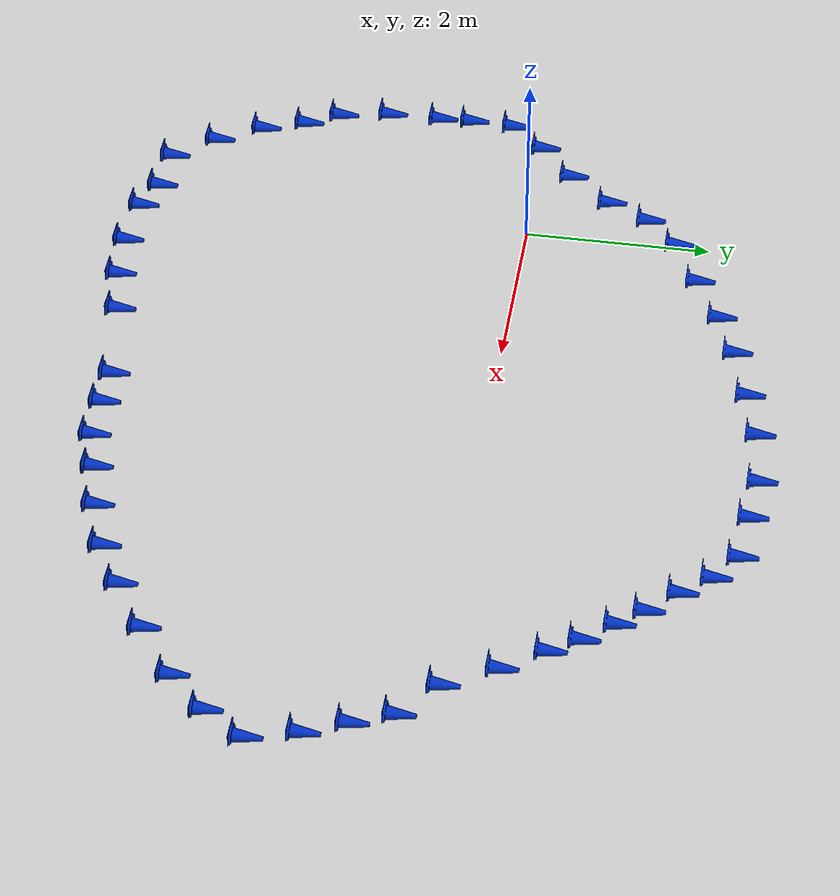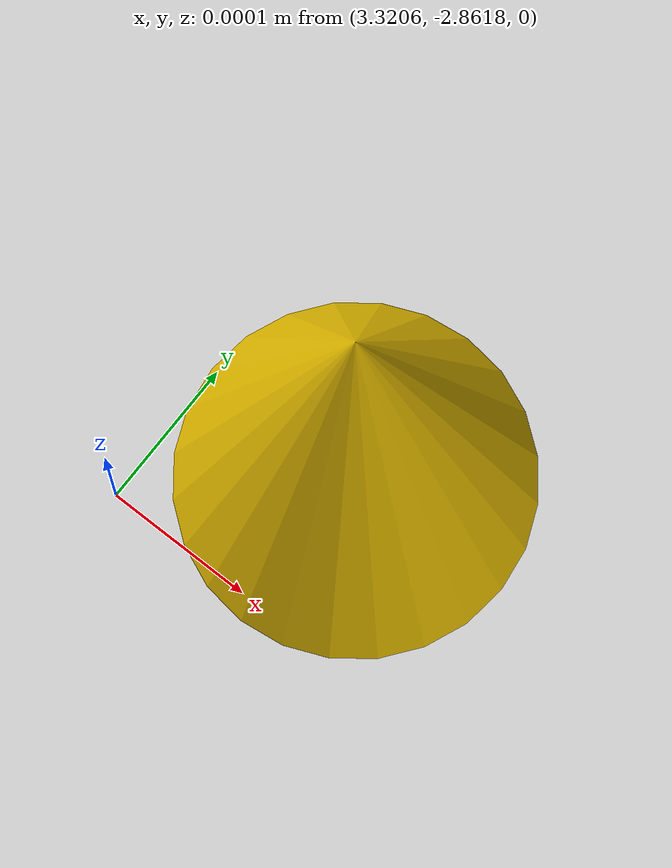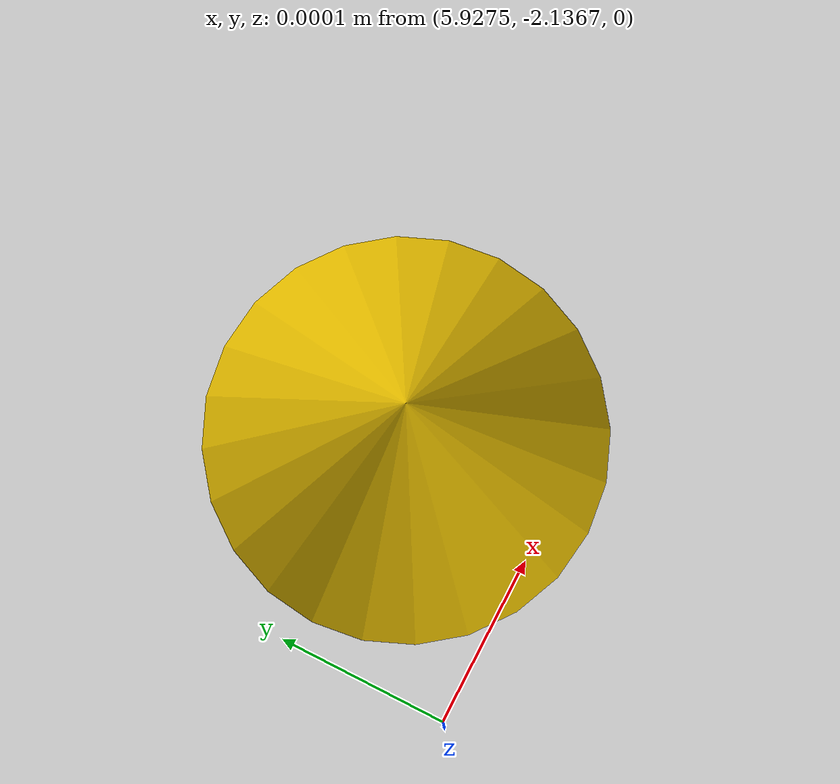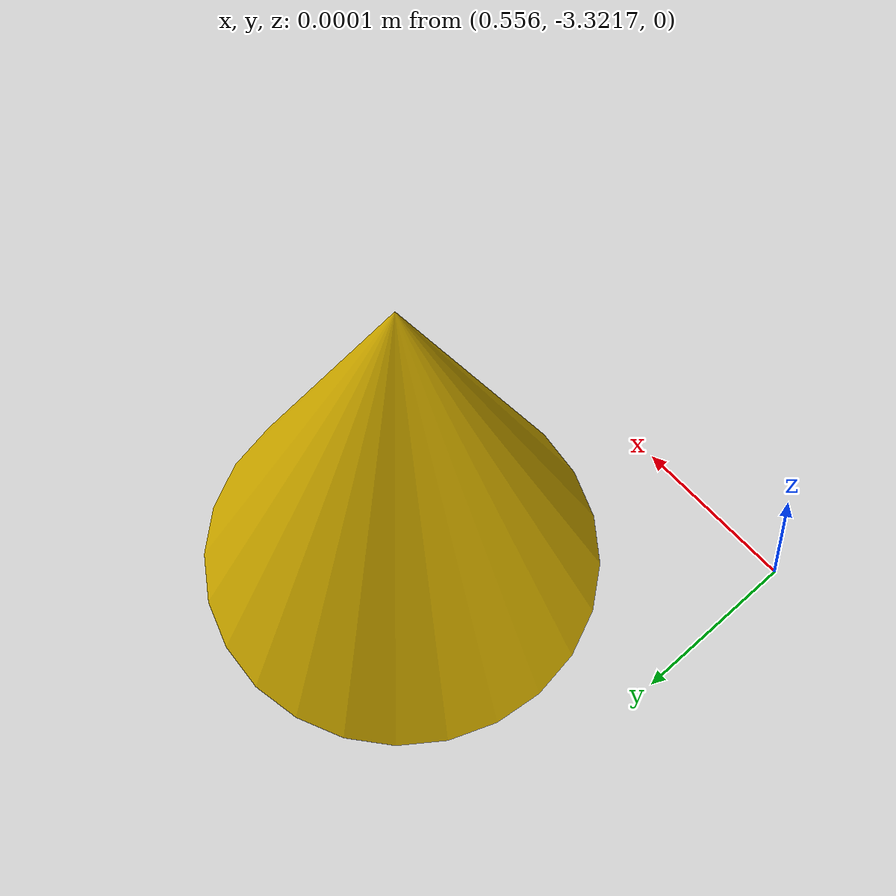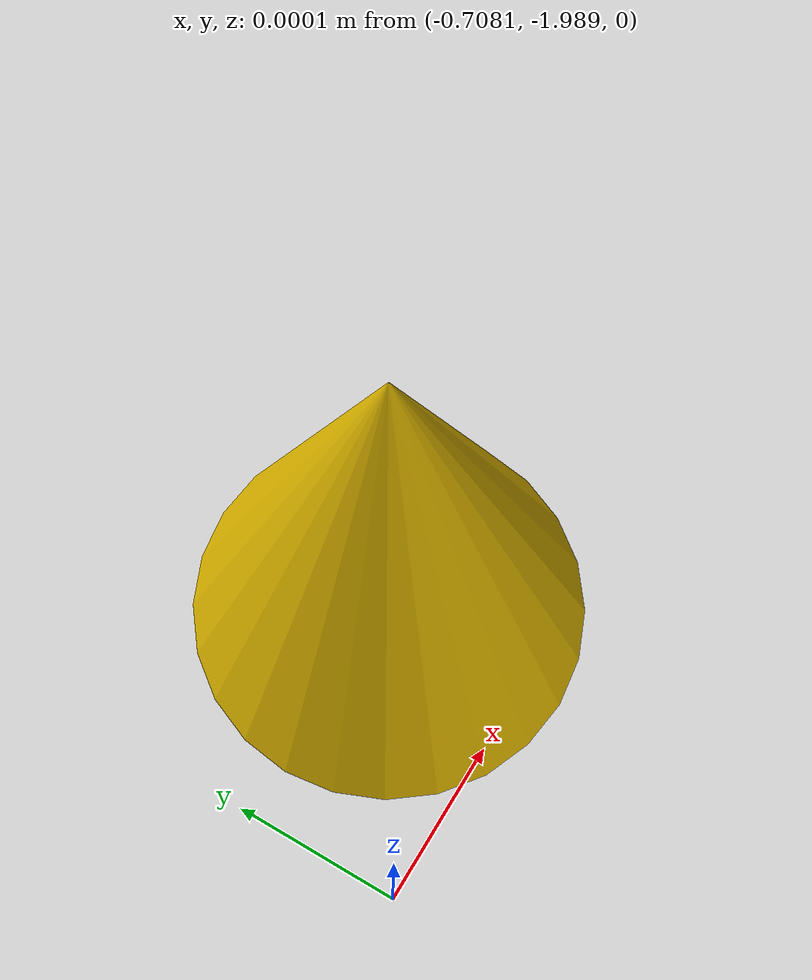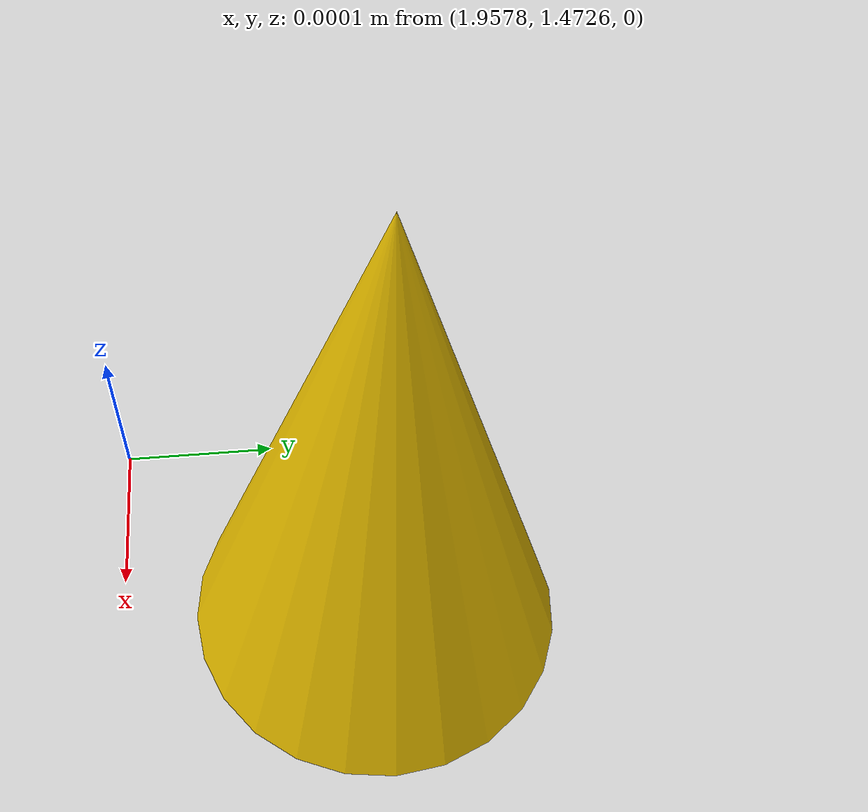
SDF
<sdf version="1.7">
 <world name="default">
  <light name="sun" type="directional">
   <pose>0 0 10 0 -0 0</pose>
   <diffuse>0.8 0.8 0.8 1</diffuse>
   <specular>0.2 0.2 0.2 1</specular>
   <attenuation>
    <range>1000</range>
    <constant>0.9</constant>
    <linear>0.01</linear>
    <quadratic>0.001</quadratic>
   </attenuation>
   <direction>-0.5 0.1 -0.9</direction>
   <spot><inner_angle>0</inner_angle><outer_angle>0</outer_angle><falloff>0</falloff></spot>
  </light>
  <model name="ground_plane">
   <static>1</static>
   <link name="link">
    <collision name="collision">
     <geometry><plane><normal>0 0 1</normal><size>100 100</size></plane></geometry>
     <surface><friction><ode><mu>100</mu><mu2>50</mu2></ode></friction></surface>
    </collision>
    <visual name="visual">
     <cast_shadows>0</cast_shadows>
     <geometry><plane><normal>0 0 1</normal><size>100 100</size></plane></geometry>
     <material>
      <script><uri>file://media/materials/scripts/gazebo.material</uri><name>Gazebo/Grey</name></script>
     </material>
    </visual>
   </link>
  </model>
  <gravity>0 0 -9.8</gravity>
  <magnetic_field>6e-06 2.3e-05 -4.2e-05</magnetic_field>
  <atmosphere type="adiabatic"/>
  <physics type="ode">
   <max_step_size>0.001</max_step_size>
   <real_time_factor>1</real_time_factor>
   <real_time_update_rate>1000</real_time_update_rate>
  </physics>
  <scene><ambient>0.4 0.4 0.4 1</ambient><background>0.7 0.7 0.7 1</background><shadows>1</shadows></scene>
  <audio><device>default</device></audio>
  <spherical_coordinates>
   <surface_model>EARTH_WGS84</surface_model>
   <latitude_deg>0</latitude_deg>
   <longitude_deg>0</longitude_deg>
   <elevation>0</elevation>
   <heading_deg>0</heading_deg>
  </spherical_coordinates>
  <model name="cone_red">
   <static>1</static>
   <link name="link">
    <visual name="visual">
     <geometry><mesh><uri>model://cone_red/meshes/cone.stl</uri><scale>0.001 0.001 0.001</scale></mesh></geometry>
     <material><ambient>1 0.2 0.1 1</ambient><diffuse>1 0.2 0.1 1</diffuse></material>
    </visual>
    <collision name="collision">
     <geometry><mesh><uri>model://cone_red/meshes/cone.stl</uri><scale>0.001 0.001 0.001</scale></mesh></geometry>
    </collision>
    <inertial>
     <mass>0.1</mass>
     <inertia><ixx>0.0001</ixx><iyy>0.0001</iyy><izz>0.0001</izz><ixy>0</ixy><ixz>0</ixz><iyz>0</iyz></inertia>
    </inertial>
   </link>
   <pose>2.38196 -4.04057 0 0 -0 0</pose>
  </model>
  <model name="cone_red_0">
   <static>1</static>
   <link name="link">
    <visual name="visual">
     <geometry><mesh><uri>model://cone_red/meshes/cone.stl</uri><scale>0.001 0.001 0.001</scale></mesh></geometry>
     <material><ambient>1 0.2 0.1 1</ambient><diffuse>1 0.2 0.1 1</diffuse></material>
    </visual>
    <collision name="collision">
     <geometry><mesh><uri>model://cone_red/meshes/cone.stl</uri><scale>0.001 0.001 0.001</scale></mesh></geometry>
    </collision>
    <inertial>
     <mass>0.1</mass>
     <inertia><ixx>0.0001</ixx><iyy>0.0001</iyy><izz>0.0001</izz><ixy>0</ixy><ixz>0</ixz><iyz>0</iyz></inertia>
    </inertial>
   </link>
   <pose>2.02926 -3.1898 0 0 -0 0</pose>
  </model>
  <model name="cone_red_0">
   <static>1</static>
   <link name="link">
    <visual name="visual">
     <geometry><mesh><uri>model://cone_red/meshes/cone.stl</uri><scale>0.001 0.001 0.001</scale></mesh></geometry>
     <material><ambient>1 0.2 0.1 1</ambient><diffuse>1 0.2 0.1 1</diffuse></material>
    </visual>
    <collision name="collision">
     <geometry><mesh><uri>model://cone_red/meshes/cone.stl</uri><scale>0.001 0.001 0.001</scale></mesh></geometry>
    </collision>
    <inertial>
     <mass>0.1</mass>
     <inertia><ixx>0.0001</ixx><iyy>0.0001</iyy><izz>0.0001</izz><ixy>0</ixy><ixz>0</ixz><iyz>0</iyz></inertia>
    </inertial>
   </link>
   <pose>2.02926 -3.1898 0 0 -0 0</pose>
  </model>
  <model name="cone_red_0">
   <static>1</static>
   <link name="link">
    <visual name="visual">
     <geometry><mesh><uri>model://cone_red/meshes/cone.stl</uri><scale>0.001 0.001 0.001</scale></mesh></geometry>
     <material><ambient>1 0.2 0.1 1</ambient><diffuse>1 0.2 0.1 1</diffuse></material>
    </visual>
    <collision name="collision">
     <geometry><mesh><uri>model://cone_red/meshes/cone.stl</uri><scale>0.001 0.001 0.001</scale></mesh></geometry>
    </collision>
    <inertial>
     <mass>0.1</mass>
     <inertia><ixx>0.0001</ixx><iyy>0.0001</iyy><izz>0.0001</izz><ixy>0</ixy><ixz>0</ixz><iyz>0</iyz></inertia>
    </inertial>
   </link>
   <pose>2.02926 -3.1898 0 0 -0 0</pose>
  </model>
  <model name="cone_blue">
   <static>1</static>
   <link name="link">
    <visual name="visual">
     <geometry><mesh><uri>model://cone_blue/meshes/cone.stl</uri><scale>0.001 0.001 0.001</scale></mesh></geometry>
     <material><ambient>0 0.2 0.8 1</ambient><diffuse>0 0.2 0.8 1</diffuse></material>
    </visual>
    <collision name="collision">
     <geometry><mesh><uri>model://cone_blue/meshes/cone.stl</uri><scale>0.001 0.001 0.001</scale></mesh></geometry>
    </collision>
    <inertial>
     <mass>0.1</mass>
     <inertia><ixx>0.0001</ixx><iyy>0.0001</iyy><izz>0.0001</izz><ixy>0</ixy><ixz>0</ixz><iyz>0</iyz></inertia>
    </inertial>
   </link>
   <pose>1.90769 -4.24948 0 0 -0 0</pose>
  </model>
  <model name="cone_blue_0">
   <static>1</static>
   <link name="link">
    <visual name="visual">
     <geometry><mesh><uri>model://cone_blue/meshes/cone.stl</uri><scale>0.001 0.001 0.001</scale></mesh></geometry>
     <material><ambient>0 0.2 0.8 1</ambient><diffuse>0 0.2 0.8 1</diffuse></material>
    </visual>
    <collision name="collision">
     <geometry><mesh><uri>model://cone_blue/meshes/cone.stl</uri><scale>0.001 0.001 0.001</scale></mesh></geometry>
    </collision>
    <inertial>
     <mass>0.1</mass>
     <inertia><ixx>0.0001</ixx><iyy>0.0001</iyy><izz>0.0001</izz><ixy>0</ixy><ixz>0</ixz><iyz>0</iyz></inertia>
    </inertial>
   </link>
   <pose>1.34019 -4.37122 0 0 -0 0</pose>
  </model>
  <model name="cone_blue_1">
   <static>1</static>
   <link name="link">
    <visual name="visual">
     <geometry><mesh><uri>model://cone_blue/meshes/cone.stl</uri><scale>0.001 0.001 0.001</scale></mesh></geometry>
     <material><ambient>0 0.2 0.8 1</ambient><diffuse>0 0.2 0.8 1</diffuse></material>
    </visual>
    <collision name="collision">
     <geometry><mesh><uri>model://cone_blue/meshes/cone.stl</uri><scale>0.001 0.001 0.001</scale></mesh></geometry>
    </collision>
    <inertial>
     <mass>0.1</mass>
     <inertia><ixx>0.0001</ixx><iyy>0.0001</iyy><izz>0.0001</izz><ixy>0</ixy><ixz>0</ixz><iyz>0</iyz></inertia>
    </inertial>
   </link>
   <pose>0.76964 -4.41472 0 0 -0 0</pose>
  </model>
  <model name="cone_blue_2">
   <static>1</static>
   <link name="link">
    <visual name="visual">
     <geometry><mesh><uri>model://cone_blue/meshes/cone.stl</uri><scale>0.001 0.001 0.001</scale></mesh></geometry>
     <material><ambient>0 0.2 0.8 1</ambient><diffuse>0 0.2 0.8 1</diffuse></material>
    </visual>
    <collision name="collision">
     <geometry><mesh><uri>model://cone_blue/meshes/cone.stl</uri><scale>0.001 0.001 0.001</scale></mesh></geometry>
    </collision>
    <inertial>
     <mass>0.1</mass>
     <inertia><ixx>0.0001</ixx><iyy>0.0001</iyy><izz>0.0001</izz><ixy>0</ixy><ixz>0</ixz><iyz>0</iyz></inertia>
    </inertial>
   </link>
   <pose>0.157789 -4.37526 0 0 -0 0</pose>
  </model>
  <model name="cone_yellow">
   <static>1</static>
   <link name="link">
    <visual name="visual">
     <geometry>
      <mesh><uri>model://cone_yellow/meshes/cone.stl</uri><scale>0.001 0.001 0.001</scale></mesh>
     </geometry>
     <material><ambient>1 0.82 0 1</ambient><diffuse>1 0.82 0 1</diffuse></material>
    </visual>
    <collision name="collision">
     <geometry>
      <mesh><uri>model://cone_yellow/meshes/cone.stl</uri><scale>0.001 0.001 0.001</scale></mesh>
     </geometry>
    </collision>
    <inertial>
     <mass>0.1</mass>
     <inertia><ixx>0.0001</ixx><iyy>0.0001</iyy><izz>0.0001</izz><ixy>0</ixy><ixz>0</ixz><iyz>0</iyz></inertia>
    </inertial>
   </link>
   <pose>1.57382 -3.09137 0 0 -0 0</pose>
  </model>
  <model name="cone_yellow_0">
   <static>1</static>
   <link name="link">
    <visual name="visual">
     <geometry>
      <mesh><uri>model://cone_yellow/meshes/cone.stl</uri><scale>0.001 0.001 0.001</scale></mesh>
     </geometry>
     <material><ambient>1 0.82 0 1</ambient><diffuse>1 0.82 0 1</diffuse></material>
    </visual>
    <collision name="collision">
     <geometry>
      <mesh><uri>model://cone_yellow/meshes/cone.stl</uri><scale>0.001 0.001 0.001</scale></mesh>
     </geometry>
    </collision>
    <inertial>
     <mass>0.1</mass>
     <inertia><ixx>0.0001</ixx><iyy>0.0001</iyy><izz>0.0001</izz><ixy>0</ixy><ixz>0</ixz><iyz>0</iyz></inertia>
    </inertial>
   </link>
   <pose>1.04145 -3.22903 0 0 -0 0</pose>
  </model>
  <model name="cone_yellow_1">
   <static>1</static>
   <link name="link">
    <visual name="visual">
     <geometry>
      <mesh><uri>model://cone_yellow/meshes/cone.stl</uri><scale>0.001 0.001 0.001</scale></mesh>
     </geometry>
     <material><ambient>1 0.82 0 1</ambient><diffuse>1 0.82 0 1</diffuse></material>
    </visual>
    <collision name="collision">
     <geometry>
      <mesh><uri>model://cone_yellow/meshes/cone.stl</uri><scale>0.001 0.001 0.001</scale></mesh>
     </geometry>
    </collision>
    <inertial>
     <mass>0.1</mass>
     <inertia><ixx>0.0001</ixx><iyy>0.0001</iyy><izz>0.0001</izz><ixy>0</ixy><ixz>0</ixz><iyz>0</iyz></inertia>
    </inertial>
   </link>
   <pose>0.556154 -3.32155 0 0 -0 0</pose>
  </model>
  <model name="cone_yellow_2">
   <static>1</static>
   <link name="link">
    <visual name="visual">
     <geometry>
      <mesh><uri>model://cone_yellow/meshes/cone.stl</uri><scale>0.001 0.001 0.001</scale></mesh>
     </geometry>
     <material><ambient>1 0.82 0 1</ambient><diffuse>1 0.82 0 1</diffuse></material>
    </visual>
    <collision name="collision">
     <geometry>
      <mesh><uri>model://cone_yellow/meshes/cone.stl</uri><scale>0.001 0.001 0.001</scale></mesh>
     </geometry>
    </collision>
    <inertial>
     <mass>0.1</mass>
     <inertia><ixx>0.0001</ixx><iyy>0.0001</iyy><izz>0.0001</izz><ixy>0</ixy><ixz>0</ixz><iyz>0</iyz></inertia>
    </inertial>
   </link>
   <pose>0.113892 -3.36991 0 0 -0 0</pose>
  </model>
  <model name="cone_yellow_3">
   <static>1</static>
   <link name="link">
    <visual name="visual">
     <geometry>
      <mesh><uri>model://cone_yellow/meshes/cone.stl</uri><scale>0.001 0.001 0.001</scale></mesh>
     </geometry>
     <material><ambient>1 0.82 0 1</ambient><diffuse>1 0.82 0 1</diffuse></material>
    </visual>
    <collision name="collision">
     <geometry>
      <mesh><uri>model://cone_yellow/meshes/cone.stl</uri><scale>0.001 0.001 0.001</scale></mesh>
     </geometry>
    </collision>
    <inertial>
     <mass>0.1</mass>
     <inertia><ixx>0.0001</ixx><iyy>0.0001</iyy><izz>0.0001</izz><ixy>0</ixy><ixz>0</ixz><iyz>0</iyz></inertia>
    </inertial>
   </link>
   <pose>-0.316793 -3.18623 0 0 -0 0</pose>
  </model>
  <model name="cone_yellow_4">
   <static>1</static>
   <link name="link">
    <visual name="visual">
     <geometry>
      <mesh><uri>model://cone_yellow/meshes/cone.stl</uri><scale>0.001 0.001 0.001</scale></mesh>
     </geometry>
     <material><ambient>1 0.82 0 1</ambient><diffuse>1 0.82 0 1</diffuse></material>
    </visual>
    <collision name="collision">
     <geometry>
      <mesh><uri>model://cone_yellow/meshes/cone.stl</uri><scale>0.001 0.001 0.001</scale></mesh>
     </geometry>
    </collision>
    <inertial>
     <mass>0.1</mass>
     <inertia><ixx>0.0001</ixx><iyy>0.0001</iyy><izz>0.0001</izz><ixy>0</ixy><ixz>0</ixz><iyz>0</iyz></inertia>
    </inertial>
   </link>
   <pose>-0.478126 -2.82781 0 0 -0 0</pose>
  </model>
  <model name="cone_yellow_5">
   <static>1</static>
   <link name="link">
    <visual name="visual">
     <geometry>
      <mesh><uri>model://cone_yellow/meshes/cone.stl</uri><scale>0.001 0.001 0.001</scale></mesh>
     </geometry>
     <material><ambient>1 0.82 0 1</ambient><diffuse>1 0.82 0 1</diffuse></material>
    </visual>
    <collision name="collision">
     <geometry>
      <mesh><uri>model://cone_yellow/meshes/cone.stl</uri><scale>0.001 0.001 0.001</scale></mesh>
     </geometry>
    </collision>
    <inertial>
     <mass>0.1</mass>
     <inertia><ixx>0.0001</ixx><iyy>0.0001</iyy><izz>0.0001</izz><ixy>0</ixy><ixz>0</ixz><iyz>0</iyz></inertia>
    </inertial>
   </link>
   <pose>-0.599837 -2.43794 0 0 -0 0</pose>
  </model>
  <model name="cone_blue_3">
   <static>1</static>
   <link name="link">
    <visual name="visual">
     <geometry><mesh><uri>model://cone_blue/meshes/cone.stl</uri><scale>0.001 0.001 0.001</scale></mesh></geometry>
     <material><ambient>0 0.2 0.8 1</ambient><diffuse>0 0.2 0.8 1</diffuse></material>
    </visual>
    <collision name="collision">
     <geometry><mesh><uri>model://cone_blue/meshes/cone.stl</uri><scale>0.001 0.001 0.001</scale></mesh></geometry>
    </collision>
    <inertial>
     <mass>0.1</mass>
     <inertia><ixx>0.0001</ixx><iyy>0.0001</iyy><izz>0.0001</izz><ixy>0</ixy><ixz>0</ixz><iyz>0</iyz></inertia>
    </inertial>
   </link>
   <pose>-0.21719 -4.24456 0 0 -0 0</pose>
  </model>
  <model name="cone_blue_4">
   <static>1</static>
   <link name="link">
    <visual name="visual">
     <geometry><mesh><uri>model://cone_blue/meshes/cone.stl</uri><scale>0.001 0.001 0.001</scale></mesh></geometry>
     <material><ambient>0 0.2 0.8 1</ambient><diffuse>0 0.2 0.8 1</diffuse></material>
    </visual>
    <collision name="collision">
     <geometry><mesh><uri>model://cone_blue/meshes/cone.stl</uri><scale>0.001 0.001 0.001</scale></mesh></geometry>
    </collision>
    <inertial>
     <mass>0.1</mass>
     <inertia><ixx>0.0001</ixx><iyy>0.0001</iyy><izz>0.0001</izz><ixy>0</ixy><ixz>0</ixz><iyz>0</iyz></inertia>
    </inertial>
   </link>
   <pose>-0.754826 -4.21696 0 0 -0 0</pose>
  </model>
  <model name="cone_blue_5">
   <static>1</static>
   <link name="link">
    <visual name="visual">
     <geometry><mesh><uri>model://cone_blue/meshes/cone.stl</uri><scale>0.001 0.001 0.001</scale></mesh></geometry>
     <material><ambient>0 0.2 0.8 1</ambient><diffuse>0 0.2 0.8 1</diffuse></material>
    </visual>
    <collision name="collision">
     <geometry><mesh><uri>model://cone_blue/meshes/cone.stl</uri><scale>0.001 0.001 0.001</scale></mesh></geometry>
    </collision>
    <inertial>
     <mass>0.1</mass>
     <inertia><ixx>0.0001</ixx><iyy>0.0001</iyy><izz>0.0001</izz><ixy>0</ixy><ixz>0</ixz><iyz>0</iyz></inertia>
    </inertial>
   </link>
   <pose>-1.11661 -3.7742 0 0 -0 0</pose>
  </model>
  <model name="cone_blue_6">
   <static>1</static>
   <link name="link">
    <visual name="visual">
     <geometry><mesh><uri>model://cone_blue/meshes/cone.stl</uri><scale>0.001 0.001 0.001</scale></mesh></geometry>
     <material><ambient>0 0.2 0.8 1</ambient><diffuse>0 0.2 0.8 1</diffuse></material>
    </visual>
    <collision name="collision">
     <geometry><mesh><uri>model://cone_blue/meshes/cone.stl</uri><scale>0.001 0.001 0.001</scale></mesh></geometry>
    </collision>
    <inertial>
     <mass>0.1</mass>
     <inertia><ixx>0.0001</ixx><iyy>0.0001</iyy><izz>0.0001</izz><ixy>0</ixy><ixz>0</ixz><iyz>0</iyz></inertia>
    </inertial>
   </link>
   <pose>-1.39974 -3.29576 0 0 -0 0</pose>
  </model>
  <model name="cone_blue_7">
   <static>1</static>
   <link name="link">
    <visual name="visual">
     <geometry><mesh><uri>model://cone_blue/meshes/cone.stl</uri><scale>0.001 0.001 0.001</scale></mesh></geometry>
     <material><ambient>0 0.2 0.8 1</ambient><diffuse>0 0.2 0.8 1</diffuse></material>
    </visual>
    <collision name="collision">
     <geometry><mesh><uri>model://cone_blue/meshes/cone.stl</uri><scale>0.001 0.001 0.001</scale></mesh></geometry>
    </collision>
    <inertial>
     <mass>0.1</mass>
     <inertia><ixx>0.0001</ixx><iyy>0.0001</iyy><izz>0.0001</izz><ixy>0</ixy><ixz>0</ixz><iyz>0</iyz></inertia>
    </inertial>
   </link>
   <pose>-1.56817 -2.83258 0 0 -0 0</pose>
  </model>
  <model name="cone_blue_8">
   <static>1</static>
   <link name="link">
    <visual name="visual">
     <geometry><mesh><uri>model://cone_blue/meshes/cone.stl</uri><scale>0.001 0.001 0.001</scale></mesh></geometry>
     <material><ambient>0 0.2 0.8 1</ambient><diffuse>0 0.2 0.8 1</diffuse></material>
    </visual>
    <collision name="collision">
     <geometry><mesh><uri>model://cone_blue/meshes/cone.stl</uri><scale>0.001 0.001 0.001</scale></mesh></geometry>
    </collision>
    <inertial>
     <mass>0.1</mass>
     <inertia><ixx>0.0001</ixx><iyy>0.0001</iyy><izz>0.0001</izz><ixy>0</ixy><ixz>0</ixz><iyz>0</iyz></inertia>
    </inertial>
   </link>
   <pose>-1.7736 -2.46659 0 0 -0 0</pose>
  </model>
  <model name="cone_yellow_6">
   <static>1</static>
   <link name="link">
    <visual name="visual">
     <geometry>
      <mesh><uri>model://cone_yellow/meshes/cone.stl</uri><scale>0.001 0.001 0.001</scale></mesh>
     </geometry>
     <material><ambient>1 0.82 0 1</ambient><diffuse>1 0.82 0 1</diffuse></material>
    </visual>
    <collision name="collision">
     <geometry>
      <mesh><uri>model://cone_yellow/meshes/cone.stl</uri><scale>0.001 0.001 0.001</scale></mesh>
     </geometry>
    </collision>
    <inertial>
     <mass>0.1</mass>
     <inertia><ixx>0.0001</ixx><iyy>0.0001</iyy><izz>0.0001</izz><ixy>0</ixy><ixz>0</ixz><iyz>0</iyz></inertia>
    </inertial>
   </link>
   <pose>-0.707955 -1.98891 0 0 -0 0</pose>
  </model>
  <model name="cone_blue_9">
   <static>1</static>
   <link name="link">
    <visual name="visual">
     <geometry><mesh><uri>model://cone_blue/meshes/cone.stl</uri><scale>0.001 0.001 0.001</scale></mesh></geometry>
     <material><ambient>0 0.2 0.8 1</ambient><diffuse>0 0.2 0.8 1</diffuse></material>
    </visual>
    <collision name="collision">
     <geometry><mesh><uri>model://cone_blue/meshes/cone.stl</uri><scale>0.001 0.001 0.001</scale></mesh></geometry>
    </collision>
    <inertial>
     <mass>0.1</mass>
     <inertia><ixx>0.0001</ixx><iyy>0.0001</iyy><izz>0.0001</izz><ixy>0</ixy><ixz>0</ixz><iyz>0</iyz></inertia>
    </inertial>
   </link>
   <pose>-1.87281 -1.91789 0 0 -0 0</pose>
  </model>
  <model name="cone_blue_10">
   <static>1</static>
   <link name="link">
    <visual name="visual">
     <geometry><mesh><uri>model://cone_blue/meshes/cone.stl</uri><scale>0.001 0.001 0.001</scale></mesh></geometry>
     <material><ambient>0 0.2 0.8 1</ambient><diffuse>0 0.2 0.8 1</diffuse></material>
    </visual>
    <collision name="collision">
     <geometry><mesh><uri>model://cone_blue/meshes/cone.stl</uri><scale>0.001 0.001 0.001</scale></mesh></geometry>
    </collision>
    <inertial>
     <mass>0.1</mass>
     <inertia><ixx>0.0001</ixx><iyy>0.0001</iyy><izz>0.0001</izz><ixy>0</ixy><ixz>0</ixz><iyz>0</iyz></inertia>
    </inertial>
   </link>
   <pose>-1.877 -1.33978 0 0 -0 0</pose>
  </model>
  <model name="cone_yellow_7">
   <static>1</static>
   <link name="link">
    <visual name="visual">
     <geometry>
      <mesh><uri>model://cone_yellow/meshes/cone.stl</uri><scale>0.001 0.001 0.001</scale></mesh>
     </geometry>
     <material><ambient>1 0.82 0 1</ambient><diffuse>1 0.82 0 1</diffuse></material>
    </visual>
    <collision name="collision">
     <geometry>
      <mesh><uri>model://cone_yellow/meshes/cone.stl</uri><scale>0.001 0.001 0.001</scale></mesh>
     </geometry>
    </collision>
    <inertial>
     <mass>0.1</mass>
     <inertia><ixx>0.0001</ixx><iyy>0.0001</iyy><izz>0.0001</izz><ixy>0</ixy><ixz>0</ixz><iyz>0</iyz></inertia>
    </inertial>
   </link>
   <pose>-0.757375 -1.57971 0 0 -0 0</pose>
  </model>
  <model name="cone_yellow_8">
   <static>1</static>
   <link name="link">
    <visual name="visual">
     <geometry>
      <mesh><uri>model://cone_yellow/meshes/cone.stl</uri><scale>0.001 0.001 0.001</scale></mesh>
     </geometry>
     <material><ambient>1 0.82 0 1</ambient><diffuse>1 0.82 0 1</diffuse></material>
    </visual>
    <collision name="collision">
     <geometry>
      <mesh><uri>model://cone_yellow/meshes/cone.stl</uri><scale>0.001 0.001 0.001</scale></mesh>
     </geometry>
    </collision>
    <inertial>
     <mass>0.1</mass>
     <inertia><ixx>0.0001</ixx><iyy>0.0001</iyy><izz>0.0001</izz><ixy>0</ixy><ixz>0</ixz><iyz>0</iyz></inertia>
    </inertial>
   </link>
   <pose>-0.820205 -1.2303 0 0 -0 0</pose>
  </model>
  <model name="cone_blue_11">
   <static>1</static>
   <link name="link">
    <visual name="visual">
     <geometry><mesh><uri>model://cone_blue/meshes/cone.stl</uri><scale>0.001 0.001 0.001</scale></mesh></geometry>
     <material><ambient>0 0.2 0.8 1</ambient><diffuse>0 0.2 0.8 1</diffuse></material>
    </visual>
    <collision name="collision">
     <geometry><mesh><uri>model://cone_blue/meshes/cone.stl</uri><scale>0.001 0.001 0.001</scale></mesh></geometry>
    </collision>
    <inertial>
     <mass>0.1</mass>
     <inertia><ixx>0.0001</ixx><iyy>0.0001</iyy><izz>0.0001</izz><ixy>0</ixy><ixz>0</ixz><iyz>0</iyz></inertia>
    </inertial>
   </link>
   <pose>-1.89009 -0.981308 0 0 -0 0</pose>
  </model>
  <model name="cone_yellow_9">
   <static>1</static>
   <link name="link">
    <visual name="visual">
     <geometry>
      <mesh><uri>model://cone_yellow/meshes/cone.stl</uri><scale>0.001 0.001 0.001</scale></mesh>
     </geometry>
     <material><ambient>1 0.82 0 1</ambient><diffuse>1 0.82 0 1</diffuse></material>
    </visual>
    <collision name="collision">
     <geometry>
      <mesh><uri>model://cone_yellow/meshes/cone.stl</uri><scale>0.001 0.001 0.001</scale></mesh>
     </geometry>
    </collision>
    <inertial>
     <mass>0.1</mass>
     <inertia><ixx>0.0001</ixx><iyy>0.0001</iyy><izz>0.0001</izz><ixy>0</ixy><ixz>0</ixz><iyz>0</iyz></inertia>
    </inertial>
   </link>
   <pose>-0.846643 -0.910144 0 0 -0 0</pose>
  </model>
  <model name="cone_blue_12">
   <static>1</static>
   <link name="link">
    <visual name="visual">
     <geometry><mesh><uri>model://cone_blue/meshes/cone.stl</uri><scale>0.001 0.001 0.001</scale></mesh></geometry>
     <material><ambient>0 0.2 0.8 1</ambient><diffuse>0 0.2 0.8 1</diffuse></material>
    </visual>
    <collision name="collision">
     <geometry><mesh><uri>model://cone_blue/meshes/cone.stl</uri><scale>0.001 0.001 0.001</scale></mesh></geometry>
    </collision>
    <inertial>
     <mass>0.1</mass>
     <inertia><ixx>0.0001</ixx><iyy>0.0001</iyy><izz>0.0001</izz><ixy>0</ixy><ixz>0</ixz><iyz>0</iyz></inertia>
    </inertial>
   </link>
   <pose>-1.86515 -0.497626 0 0 -0 0</pose>
  </model>
  <model name="cone_yellow_10">
   <static>1</static>
   <link name="link">
    <visual name="visual">
     <geometry>
      <mesh><uri>model://cone_yellow/meshes/cone.stl</uri><scale>0.001 0.001 0.001</scale></mesh>
     </geometry>
     <material><ambient>1 0.82 0 1</ambient><diffuse>1 0.82 0 1</diffuse></material>
    </visual>
    <collision name="collision">
     <geometry>
      <mesh><uri>model://cone_yellow/meshes/cone.stl</uri><scale>0.001 0.001 0.001</scale></mesh>
     </geometry>
    </collision>
    <inertial>
     <mass>0.1</mass>
     <inertia><ixx>0.0001</ixx><iyy>0.0001</iyy><izz>0.0001</izz><ixy>0</ixy><ixz>0</ixz><iyz>0</iyz></inertia>
    </inertial>
   </link>
   <pose>-0.6794 -0.614028 0 0 -0 0</pose>
  </model>
  <model name="cone_yellow_11">
   <static>1</static>
   <link name="link">
    <visual name="visual">
     <geometry>
      <mesh><uri>model://cone_yellow/meshes/cone.stl</uri><scale>0.001 0.001 0.001</scale></mesh>
     </geometry>
     <material><ambient>1 0.82 0 1</ambient><diffuse>1 0.82 0 1</diffuse></material>
    </visual>
    <collision name="collision">
     <geometry>
      <mesh><uri>model://cone_yellow/meshes/cone.stl</uri><scale>0.001 0.001 0.001</scale></mesh>
     </geometry>
    </collision>
    <inertial>
     <mass>0.1</mass>
     <inertia><ixx>0.0001</ixx><iyy>0.0001</iyy><izz>0.0001</izz><ixy>0</ixy><ixz>0</ixz><iyz>0</iyz></inertia>
    </inertial>
   </link>
   <pose>-0.305017 -0.216786 0 0 -0 0</pose>
  </model>
  <model name="cone_yellow_12">
   <static>1</static>
   <link name="link">
    <visual name="visual">
     <geometry>
      <mesh><uri>model://cone_yellow/meshes/cone.stl</uri><scale>0.001 0.001 0.001</scale></mesh>
     </geometry>
     <material><ambient>1 0.82 0 1</ambient><diffuse>1 0.82 0 1</diffuse></material>
    </visual>
    <collision name="collision">
     <geometry>
      <mesh><uri>model://cone_yellow/meshes/cone.stl</uri><scale>0.001 0.001 0.001</scale></mesh>
     </geometry>
    </collision>
    <inertial>
     <mass>0.1</mass>
     <inertia><ixx>0.0001</ixx><iyy>0.0001</iyy><izz>0.0001</izz><ixy>0</ixy><ixz>0</ixz><iyz>0</iyz></inertia>
    </inertial>
   </link>
   <pose>0.183364 0.137115 0 0 -0 0</pose>
  </model>
  <model name="cone_yellow_13">
   <static>1</static>
   <link name="link">
    <visual name="visual">
     <geometry>
      <mesh><uri>model://cone_yellow/meshes/cone.stl</uri><scale>0.001 0.001 0.001</scale></mesh>
     </geometry>
     <material><ambient>1 0.82 0 1</ambient><diffuse>1 0.82 0 1</diffuse></material>
    </visual>
    <collision name="collision">
     <geometry>
      <mesh><uri>model://cone_yellow/meshes/cone.stl</uri><scale>0.001 0.001 0.001</scale></mesh>
     </geometry>
    </collision>
    <inertial>
     <mass>0.1</mass>
     <inertia><ixx>0.0001</ixx><iyy>0.0001</iyy><izz>0.0001</izz><ixy>0</ixy><ixz>0</ixz><iyz>0</iyz></inertia>
    </inertial>
   </link>
   <pose>0.452957 0.528009 0 0 -0 0</pose>
  </model>
  <model name="cone_yellow_14">
   <static>1</static>
   <link name="link">
    <visual name="visual">
     <geometry>
      <mesh><uri>model://cone_yellow/meshes/cone.stl</uri><scale>0.001 0.001 0.001</scale></mesh>
     </geometry>
     <material><ambient>1 0.82 0 1</ambient><diffuse>1 0.82 0 1</diffuse></material>
    </visual>
    <collision name="collision">
     <geometry>
      <mesh><uri>model://cone_yellow/meshes/cone.stl</uri><scale>0.001 0.001 0.001</scale></mesh>
     </geometry>
    </collision>
    <inertial>
     <mass>0.1</mass>
     <inertia><ixx>0.0001</ixx><iyy>0.0001</iyy><izz>0.0001</izz><ixy>0</ixy><ixz>0</ixz><iyz>0</iyz></inertia>
    </inertial>
   </link>
   <pose>0.6839 0.91515 0 0 -0 0</pose>
  </model>
  <model name="cone_blue_13">
   <static>1</static>
   <link name="link">
    <visual name="visual">
     <geometry><mesh><uri>model://cone_blue/meshes/cone.stl</uri><scale>0.001 0.001 0.001</scale></mesh></geometry>
     <material><ambient>0 0.2 0.8 1</ambient><diffuse>0 0.2 0.8 1</diffuse></material>
    </visual>
    <collision name="collision">
     <geometry><mesh><uri>model://cone_blue/meshes/cone.stl</uri><scale>0.001 0.001 0.001</scale></mesh></geometry>
    </collision>
    <inertial>
     <mass>0.1</mass>
     <inertia><ixx>0.0001</ixx><iyy>0.0001</iyy><izz>0.0001</izz><ixy>0</ixy><ixz>0</ixz><iyz>0</iyz></inertia>
    </inertial>
   </link>
   <pose>-1.52448 -0.115332 0 0 -0 0</pose>
  </model>
  <model name="cone_blue_14">
   <static>1</static>
   <link name="link">
    <visual name="visual">
     <geometry><mesh><uri>model://cone_blue/meshes/cone.stl</uri><scale>0.001 0.001 0.001</scale></mesh></geometry>
     <material><ambient>0 0.2 0.8 1</ambient><diffuse>0 0.2 0.8 1</diffuse></material>
    </visual>
    <collision name="collision">
     <geometry><mesh><uri>model://cone_blue/meshes/cone.stl</uri><scale>0.001 0.001 0.001</scale></mesh></geometry>
    </collision>
    <inertial>
     <mass>0.1</mass>
     <inertia><ixx>0.0001</ixx><iyy>0.0001</iyy><izz>0.0001</izz><ixy>0</ixy><ixz>0</ixz><iyz>0</iyz></inertia>
    </inertial>
   </link>
   <pose>-1.07369 0.262376 0 0 -0 0</pose>
  </model>
  <model name="cone_blue_15">
   <static>1</static>
   <link name="link">
    <visual name="visual">
     <geometry><mesh><uri>model://cone_blue/meshes/cone.stl</uri><scale>0.001 0.001 0.001</scale></mesh></geometry>
     <material><ambient>0 0.2 0.8 1</ambient><diffuse>0 0.2 0.8 1</diffuse></material>
    </visual>
    <collision name="collision">
     <geometry><mesh><uri>model://cone_blue/meshes/cone.stl</uri><scale>0.001 0.001 0.001</scale></mesh></geometry>
    </collision>
    <inertial>
     <mass>0.1</mass>
     <inertia><ixx>0.0001</ixx><iyy>0.0001</iyy><izz>0.0001</izz><ixy>0</ixy><ixz>0</ixz><iyz>0</iyz></inertia>
    </inertial>
   </link>
   <pose>-0.679495 0.736334 0 0 -0 0</pose>
  </model>
  <model name="cone_blue_16">
   <static>1</static>
   <link name="link">
    <visual name="visual">
     <geometry><mesh><uri>model://cone_blue/meshes/cone.stl</uri><scale>0.001 0.001 0.001</scale></mesh></geometry>
     <material><ambient>0 0.2 0.8 1</ambient><diffuse>0 0.2 0.8 1</diffuse></material>
    </visual>
    <collision name="collision">
     <geometry><mesh><uri>model://cone_blue/meshes/cone.stl</uri><scale>0.001 0.001 0.001</scale></mesh></geometry>
    </collision>
    <inertial>
     <mass>0.1</mass>
     <inertia><ixx>0.0001</ixx><iyy>0.0001</iyy><izz>0.0001</izz><ixy>0</ixy><ixz>0</ixz><iyz>0</iyz></inertia>
    </inertial>
   </link>
   <pose>-0.440208 1.195 0 0 -0 0</pose>
  </model>
  <model name="cone_blue_17">
   <static>1</static>
   <link name="link">
    <visual name="visual">
     <geometry><mesh><uri>model://cone_blue/meshes/cone.stl</uri><scale>0.001 0.001 0.001</scale></mesh></geometry>
     <material><ambient>0 0.2 0.8 1</ambient><diffuse>0 0.2 0.8 1</diffuse></material>
    </visual>
    <collision name="collision">
     <geometry><mesh><uri>model://cone_blue/meshes/cone.stl</uri><scale>0.001 0.001 0.001</scale></mesh></geometry>
    </collision>
    <inertial>
     <mass>0.1</mass>
     <inertia><ixx>0.0001</ixx><iyy>0.0001</iyy><izz>0.0001</izz><ixy>0</ixy><ixz>0</ixz><iyz>0</iyz></inertia>
    </inertial>
   </link>
   <pose>-0.072735 1.54896 0 0 -0 0</pose>
  </model>
  <model name="cone_yellow_15">
   <static>1</static>
   <link name="link">
    <visual name="visual">
     <geometry>
      <mesh><uri>model://cone_yellow/meshes/cone.stl</uri><scale>0.001 0.001 0.001</scale></mesh>
     </geometry>
     <material><ambient>1 0.82 0 1</ambient><diffuse>1 0.82 0 1</diffuse></material>
    </visual>
    <collision name="collision">
     <geometry>
      <mesh><uri>model://cone_yellow/meshes/cone.stl</uri><scale>0.001 0.001 0.001</scale></mesh>
     </geometry>
    </collision>
    <inertial>
     <mass>0.1</mass>
     <inertia><ixx>0.0001</ixx><iyy>0.0001</iyy><izz>0.0001</izz><ixy>0</ixy><ixz>0</ixz><iyz>0</iyz></inertia>
    </inertial>
   </link>
   <pose>0.99672 1.14996 0 0 -0 0</pose>
  </model>
  <model name="cone_yellow_16">
   <static>1</static>
   <link name="link">
    <visual name="visual">
     <geometry>
      <mesh><uri>model://cone_yellow/meshes/cone.stl</uri><scale>0.001 0.001 0.001</scale></mesh>
     </geometry>
     <material><ambient>1 0.82 0 1</ambient><diffuse>1 0.82 0 1</diffuse></material>
    </visual>
    <collision name="collision">
     <geometry>
      <mesh><uri>model://cone_yellow/meshes/cone.stl</uri><scale>0.001 0.001 0.001</scale></mesh>
     </geometry>
    </collision>
    <inertial>
     <mass>0.1</mass>
     <inertia><ixx>0.0001</ixx><iyy>0.0001</iyy><izz>0.0001</izz><ixy>0</ixy><ixz>0</ixz><iyz>0</iyz></inertia>
    </inertial>
   </link>
   <pose>1.44594 1.35134 0 0 -0 0</pose>
  </model>
  <model name="cone_yellow_17">
   <static>1</static>
   <link name="link">
    <visual name="visual">
     <geometry>
      <mesh><uri>model://cone_yellow/meshes/cone.stl</uri><scale>0.001 0.001 0.001</scale></mesh>
     </geometry>
     <material><ambient>1 0.82 0 1</ambient><diffuse>1 0.82 0 1</diffuse></material>
    </visual>
    <collision name="collision">
     <geometry>
      <mesh><uri>model://cone_yellow/meshes/cone.stl</uri><scale>0.001 0.001 0.001</scale></mesh>
     </geometry>
    </collision>
    <inertial>
     <mass>0.1</mass>
     <inertia><ixx>0.0001</ixx><iyy>0.0001</iyy><izz>0.0001</izz><ixy>0</ixy><ixz>0</ixz><iyz>0</iyz></inertia>
    </inertial>
   </link>
   <pose>1.95793 1.47276 0 0 -0 0</pose>
  </model>
  <model name="cone_yellow_18">
   <static>1</static>
   <link name="link">
    <visual name="visual">
     <geometry>
      <mesh><uri>model://cone_yellow/meshes/cone.stl</uri><scale>0.001 0.001 0.001</scale></mesh>
     </geometry>
     <material><ambient>1 0.82 0 1</ambient><diffuse>1 0.82 0 1</diffuse></material>
    </visual>
    <collision name="collision">
     <geometry>
      <mesh><uri>model://cone_yellow/meshes/cone.stl</uri><scale>0.001 0.001 0.001</scale></mesh>
     </geometry>
    </collision>
    <inertial>
     <mass>0.1</mass>
     <inertia><ixx>0.0001</ixx><iyy>0.0001</iyy><izz>0.0001</izz><ixy>0</ixy><ixz>0</ixz><iyz>0</iyz></inertia>
    </inertial>
   </link>
   <pose>2.50472 1.63676 0 0 -0 0</pose>
  </model>
  <model name="cone_yellow_19">
   <static>1</static>
   <link name="link">
    <visual name="visual">
     <geometry>
      <mesh><uri>model://cone_yellow/meshes/cone.stl</uri><scale>0.001 0.001 0.001</scale></mesh>
     </geometry>
     <material><ambient>1 0.82 0 1</ambient><diffuse>1 0.82 0 1</diffuse></material>
    </visual>
    <collision name="collision">
     <geometry>
      <mesh><uri>model://cone_yellow/meshes/cone.stl</uri><scale>0.001 0.001 0.001</scale></mesh>
     </geometry>
    </collision>
    <inertial>
     <mass>0.1</mass>
     <inertia><ixx>0.0001</ixx><iyy>0.0001</iyy><izz>0.0001</izz><ixy>0</ixy><ixz>0</ixz><iyz>0</iyz></inertia>
    </inertial>
   </link>
   <pose>3.24892 1.78128 0 0 -0 0</pose>
  </model>
  <model name="cone_yellow_20">
   <static>1</static>
   <link name="link">
    <visual name="visual">
     <geometry>
      <mesh><uri>model://cone_yellow/meshes/cone.stl</uri><scale>0.001 0.001 0.001</scale></mesh>
     </geometry>
     <material><ambient>1 0.82 0 1</ambient><diffuse>1 0.82 0 1</diffuse></material>
    </visual>
    <collision name="collision">
     <geometry>
      <mesh><uri>model://cone_yellow/meshes/cone.stl</uri><scale>0.001 0.001 0.001</scale></mesh>
     </geometry>
    </collision>
    <inertial>
     <mass>0.1</mass>
     <inertia><ixx>0.0001</ixx><iyy>0.0001</iyy><izz>0.0001</izz><ixy>0</ixy><ixz>0</ixz><iyz>0</iyz></inertia>
    </inertial>
   </link>
   <pose>3.88565 1.86419 0 0 -0 0</pose>
  </model>
  <model name="cone_blue_18">
   <static>1</static>
   <link name="link">
    <visual name="visual">
     <geometry><mesh><uri>model://cone_blue/meshes/cone.stl</uri><scale>0.001 0.001 0.001</scale></mesh></geometry>
     <material><ambient>0 0.2 0.8 1</ambient><diffuse>0 0.2 0.8 1</diffuse></material>
    </visual>
    <collision name="collision">
     <geometry><mesh><uri>model://cone_blue/meshes/cone.stl</uri><scale>0.001 0.001 0.001</scale></mesh></geometry>
    </collision>
    <inertial>
     <mass>0.1</mass>
     <inertia><ixx>0.0001</ixx><iyy>0.0001</iyy><izz>0.0001</izz><ixy>0</ixy><ixz>0</ixz><iyz>0</iyz></inertia>
    </inertial>
   </link>
   <pose>0.501366 1.83329 0 0 -0 0</pose>
  </model>
  <model name="cone_blue_19">
   <static>1</static>
   <link name="link">
    <visual name="visual">
     <geometry><mesh><uri>model://cone_blue/meshes/cone.stl</uri><scale>0.001 0.001 0.001</scale></mesh></geometry>
     <material><ambient>0 0.2 0.8 1</ambient><diffuse>0 0.2 0.8 1</diffuse></material>
    </visual>
    <collision name="collision">
     <geometry><mesh><uri>model://cone_blue/meshes/cone.stl</uri><scale>0.001 0.001 0.001</scale></mesh></geometry>
    </collision>
    <inertial>
     <mass>0.1</mass>
     <inertia><ixx>0.0001</ixx><iyy>0.0001</iyy><izz>0.0001</izz><ixy>0</ixy><ixz>0</ixz><iyz>0</iyz></inertia>
    </inertial>
   </link>
   <pose>1.05927 2.12401 0 0 -0 0</pose>
  </model>
  <model name="cone_blue_20">
   <static>1</static>
   <link name="link">
    <visual name="visual">
     <geometry><mesh><uri>model://cone_blue/meshes/cone.stl</uri><scale>0.001 0.001 0.001</scale></mesh></geometry>
     <material><ambient>0 0.2 0.8 1</ambient><diffuse>0 0.2 0.8 1</diffuse></material>
    </visual>
    <collision name="collision">
     <geometry><mesh><uri>model://cone_blue/meshes/cone.stl</uri><scale>0.001 0.001 0.001</scale></mesh></geometry>
    </collision>
    <inertial>
     <mass>0.1</mass>
     <inertia><ixx>0.0001</ixx><iyy>0.0001</iyy><izz>0.0001</izz><ixy>0</ixy><ixz>0</ixz><iyz>0</iyz></inertia>
    </inertial>
   </link>
   <pose>1.59744 2.33822 0 0 -0 0</pose>
  </model>
  <model name="cone_blue_21">
   <static>1</static>
   <link name="link">
    <visual name="visual">
     <geometry><mesh><uri>model://cone_blue/meshes/cone.stl</uri><scale>0.001 0.001 0.001</scale></mesh></geometry>
     <material><ambient>0 0.2 0.8 1</ambient><diffuse>0 0.2 0.8 1</diffuse></material>
    </visual>
    <collision name="collision">
     <geometry><mesh><uri>model://cone_blue/meshes/cone.stl</uri><scale>0.001 0.001 0.001</scale></mesh></geometry>
    </collision>
    <inertial>
     <mass>0.1</mass>
     <inertia><ixx>0.0001</ixx><iyy>0.0001</iyy><izz>0.0001</izz><ixy>0</ixy><ixz>0</ixz><iyz>0</iyz></inertia>
    </inertial>
   </link>
   <pose>2.23956 2.53108 0 0 -0 0</pose>
  </model>
  <model name="cone_blue_22">
   <static>1</static>
   <link name="link">
    <visual name="visual">
     <geometry><mesh><uri>model://cone_blue/meshes/cone.stl</uri><scale>0.001 0.001 0.001</scale></mesh></geometry>
     <material><ambient>0 0.2 0.8 1</ambient><diffuse>0 0.2 0.8 1</diffuse></material>
    </visual>
    <collision name="collision">
     <geometry><mesh><uri>model://cone_blue/meshes/cone.stl</uri><scale>0.001 0.001 0.001</scale></mesh></geometry>
    </collision>
    <inertial>
     <mass>0.1</mass>
     <inertia><ixx>0.0001</ixx><iyy>0.0001</iyy><izz>0.0001</izz><ixy>0</ixy><ixz>0</ixz><iyz>0</iyz></inertia>
    </inertial>
   </link>
   <pose>2.83032 2.68776 0 0 -0 0</pose>
  </model>
  <model name="cone_blue_23">
   <static>1</static>
   <link name="link">
    <visual name="visual">
     <geometry><mesh><uri>model://cone_blue/meshes/cone.stl</uri><scale>0.001 0.001 0.001</scale></mesh></geometry>
     <material><ambient>0 0.2 0.8 1</ambient><diffuse>0 0.2 0.8 1</diffuse></material>
    </visual>
    <collision name="collision">
     <geometry><mesh><uri>model://cone_blue/meshes/cone.stl</uri><scale>0.001 0.001 0.001</scale></mesh></geometry>
    </collision>
    <inertial>
     <mass>0.1</mass>
     <inertia><ixx>0.0001</ixx><iyy>0.0001</iyy><izz>0.0001</izz><ixy>0</ixy><ixz>0</ixz><iyz>0</iyz></inertia>
    </inertial>
   </link>
   <pose>3.5225 2.76821 0 0 -0 0</pose>
  </model>
  <model name="cone_blue_24">
   <static>1</static>
   <link name="link">
    <visual name="visual">
     <geometry><mesh><uri>model://cone_blue/meshes/cone.stl</uri><scale>0.001 0.001 0.001</scale></mesh></geometry>
     <material><ambient>0 0.2 0.8 1</ambient><diffuse>0 0.2 0.8 1</diffuse></material>
    </visual>
    <collision name="collision">
     <geometry><mesh><uri>model://cone_blue/meshes/cone.stl</uri><scale>0.001 0.001 0.001</scale></mesh></geometry>
    </collision>
    <inertial>
     <mass>0.1</mass>
     <inertia><ixx>0.0001</ixx><iyy>0.0001</iyy><izz>0.0001</izz><ixy>0</ixy><ixz>0</ixz><iyz>0</iyz></inertia>
    </inertial>
   </link>
   <pose>4.05487 2.72312 0 0 -0 0</pose>
  </model>
  <model name="cone_blue_25">
   <static>1</static>
   <link name="link">
    <visual name="visual">
     <geometry><mesh><uri>model://cone_blue/meshes/cone.stl</uri><scale>0.001 0.001 0.001</scale></mesh></geometry>
     <material><ambient>0 0.2 0.8 1</ambient><diffuse>0 0.2 0.8 1</diffuse></material>
    </visual>
    <collision name="collision">
     <geometry><mesh><uri>model://cone_blue/meshes/cone.stl</uri><scale>0.001 0.001 0.001</scale></mesh></geometry>
    </collision>
    <inertial>
     <mass>0.1</mass>
     <inertia><ixx>0.0001</ixx><iyy>0.0001</iyy><izz>0.0001</izz><ixy>0</ixy><ixz>0</ixz><iyz>0</iyz></inertia>
    </inertial>
   </link>
   <pose>4.63085 2.67058 0 0 -0 0</pose>
  </model>
  <model name="cone_yellow_21">
   <static>1</static>
   <link name="link">
    <visual name="visual">
     <geometry>
      <mesh><uri>model://cone_yellow/meshes/cone.stl</uri><scale>0.001 0.001 0.001</scale></mesh>
     </geometry>
     <material><ambient>1 0.82 0 1</ambient><diffuse>1 0.82 0 1</diffuse></material>
    </visual>
    <collision name="collision">
     <geometry>
      <mesh><uri>model://cone_yellow/meshes/cone.stl</uri><scale>0.001 0.001 0.001</scale></mesh>
     </geometry>
    </collision>
    <inertial>
     <mass>0.1</mass>
     <inertia><ixx>0.0001</ixx><iyy>0.0001</iyy><izz>0.0001</izz><ixy>0</ixy><ixz>0</ixz><iyz>0</iyz></inertia>
    </inertial>
   </link>
   <pose>4.29103 1.55969 0 0 -0 0</pose>
  </model>
  <model name="cone_yellow_22">
   <static>1</static>
   <link name="link">
    <visual name="visual">
     <geometry>
      <mesh><uri>model://cone_yellow/meshes/cone.stl</uri><scale>0.001 0.001 0.001</scale></mesh>
     </geometry>
     <material><ambient>1 0.82 0 1</ambient><diffuse>1 0.82 0 1</diffuse></material>
    </visual>
    <collision name="collision">
     <geometry>
      <mesh><uri>model://cone_yellow/meshes/cone.stl</uri><scale>0.001 0.001 0.001</scale></mesh>
     </geometry>
    </collision>
    <inertial>
     <mass>0.1</mass>
     <inertia><ixx>0.0001</ixx><iyy>0.0001</iyy><izz>0.0001</izz><ixy>0</ixy><ixz>0</ixz><iyz>0</iyz></inertia>
    </inertial>
   </link>
   <pose>4.61404 1.13789 0 0 -0 0</pose>
  </model>
  <model name="cone_yellow_23">
   <static>1</static>
   <link name="link">
    <visual name="visual">
     <geometry>
      <mesh><uri>model://cone_yellow/meshes/cone.stl</uri><scale>0.001 0.001 0.001</scale></mesh>
     </geometry>
     <material><ambient>1 0.82 0 1</ambient><diffuse>1 0.82 0 1</diffuse></material>
    </visual>
    <collision name="collision">
     <geometry>
      <mesh><uri>model://cone_yellow/meshes/cone.stl</uri><scale>0.001 0.001 0.001</scale></mesh>
     </geometry>
    </collision>
    <inertial>
     <mass>0.1</mass>
     <inertia><ixx>0.0001</ixx><iyy>0.0001</iyy><izz>0.0001</izz><ixy>0</ixy><ixz>0</ixz><iyz>0</iyz></inertia>
    </inertial>
   </link>
   <pose>4.92523 0.832387 0 0 -0 0</pose>
  </model>
  <model name="cone_yellow_24">
   <static>1</static>
   <link name="link">
    <visual name="visual">
     <geometry>
      <mesh><uri>model://cone_yellow/meshes/cone.stl</uri><scale>0.001 0.001 0.001</scale></mesh>
     </geometry>
     <material><ambient>1 0.82 0 1</ambient><diffuse>1 0.82 0 1</diffuse></material>
    </visual>
    <collision name="collision">
     <geometry>
      <mesh><uri>model://cone_yellow/meshes/cone.stl</uri><scale>0.001 0.001 0.001</scale></mesh>
     </geometry>
    </collision>
    <inertial>
     <mass>0.1</mass>
     <inertia><ixx>0.0001</ixx><iyy>0.0001</iyy><izz>0.0001</izz><ixy>0</ixy><ixz>0</ixz><iyz>0</iyz></inertia>
    </inertial>
   </link>
   <pose>5.1515 0.596885 0 0 -0 0</pose>
  </model>
  <model name="cone_yellow_25">
   <static>1</static>
   <link name="link">
    <visual name="visual">
     <geometry>
      <mesh><uri>model://cone_yellow/meshes/cone.stl</uri><scale>0.001 0.001 0.001</scale></mesh>
     </geometry>
     <material><ambient>1 0.82 0 1</ambient><diffuse>1 0.82 0 1</diffuse></material>
    </visual>
    <collision name="collision">
     <geometry>
      <mesh><uri>model://cone_yellow/meshes/cone.stl</uri><scale>0.001 0.001 0.001</scale></mesh>
     </geometry>
    </collision>
    <inertial>
     <mass>0.1</mass>
     <inertia><ixx>0.0001</ixx><iyy>0.0001</iyy><izz>0.0001</izz><ixy>0</ixy><ixz>0</ixz><iyz>0</iyz></inertia>
    </inertial>
   </link>
   <pose>5.49886 0.240595 0 0 -0 0</pose>
  </model>
  <model name="cone_blue_26">
   <static>1</static>
   <link name="link">
    <visual name="visual">
     <geometry><mesh><uri>model://cone_blue/meshes/cone.stl</uri><scale>0.001 0.001 0.001</scale></mesh></geometry>
     <material><ambient>0 0.2 0.8 1</ambient><diffuse>0 0.2 0.8 1</diffuse></material>
    </visual>
    <collision name="collision">
     <geometry><mesh><uri>model://cone_blue/meshes/cone.stl</uri><scale>0.001 0.001 0.001</scale></mesh></geometry>
    </collision>
    <inertial>
     <mass>0.1</mass>
     <inertia><ixx>0.0001</ixx><iyy>0.0001</iyy><izz>0.0001</izz><ixy>0</ixy><ixz>0</ixz><iyz>0</iyz></inertia>
    </inertial>
   </link>
   <pose>4.9622 2.44095 0 0 -0 0</pose>
  </model>
  <model name="cone_blue_27">
   <static>1</static>
   <link name="link">
    <visual name="visual">
     <geometry><mesh><uri>model://cone_blue/meshes/cone.stl</uri><scale>0.001 0.001 0.001</scale></mesh></geometry>
     <material><ambient>0 0.2 0.8 1</ambient><diffuse>0 0.2 0.8 1</diffuse></material>
    </visual>
    <collision name="collision">
     <geometry><mesh><uri>model://cone_blue/meshes/cone.stl</uri><scale>0.001 0.001 0.001</scale></mesh></geometry>
    </collision>
    <inertial>
     <mass>0.1</mass>
     <inertia><ixx>0.0001</ixx><iyy>0.0001</iyy><izz>0.0001</izz><ixy>0</ixy><ixz>0</ixz><iyz>0</iyz></inertia>
    </inertial>
   </link>
   <pose>5.21867 2.13742 0 0 -0 0</pose>
  </model>
  <model name="cone_blue_28">
   <static>1</static>
   <link name="link">
    <visual name="visual">
     <geometry><mesh><uri>model://cone_blue/meshes/cone.stl</uri><scale>0.001 0.001 0.001</scale></mesh></geometry>
     <material><ambient>0 0.2 0.8 1</ambient><diffuse>0 0.2 0.8 1</diffuse></material>
    </visual>
    <collision name="collision">
     <geometry><mesh><uri>model://cone_blue/meshes/cone.stl</uri><scale>0.001 0.001 0.001</scale></mesh></geometry>
    </collision>
    <inertial>
     <mass>0.1</mass>
     <inertia><ixx>0.0001</ixx><iyy>0.0001</iyy><izz>0.0001</izz><ixy>0</ixy><ixz>0</ixz><iyz>0</iyz></inertia>
    </inertial>
   </link>
   <pose>5.51371 1.83791 0 0 -0 0</pose>
  </model>
  <model name="cone_blue_29">
   <static>1</static>
   <link name="link">
    <visual name="visual">
     <geometry><mesh><uri>model://cone_blue/meshes/cone.stl</uri><scale>0.001 0.001 0.001</scale></mesh></geometry>
     <material><ambient>0 0.2 0.8 1</ambient><diffuse>0 0.2 0.8 1</diffuse></material>
    </visual>
    <collision name="collision">
     <geometry><mesh><uri>model://cone_blue/meshes/cone.stl</uri><scale>0.001 0.001 0.001</scale></mesh></geometry>
    </collision>
    <inertial>
     <mass>0.1</mass>
     <inertia><ixx>0.0001</ixx><iyy>0.0001</iyy><izz>0.0001</izz><ixy>0</ixy><ixz>0</ixz><iyz>0</iyz></inertia>
    </inertial>
   </link>
   <pose>5.73875 1.57462 0 0 -0 0</pose>
  </model>
  <model name="cone_blue_30">
   <static>1</static>
   <link name="link">
    <visual name="visual">
     <geometry><mesh><uri>model://cone_blue/meshes/cone.stl</uri><scale>0.001 0.001 0.001</scale></mesh></geometry>
     <material><ambient>0 0.2 0.8 1</ambient><diffuse>0 0.2 0.8 1</diffuse></material>
    </visual>
    <collision name="collision">
     <geometry><mesh><uri>model://cone_blue/meshes/cone.stl</uri><scale>0.001 0.001 0.001</scale></mesh></geometry>
    </collision>
    <inertial>
     <mass>0.1</mass>
     <inertia><ixx>0.0001</ixx><iyy>0.0001</iyy><izz>0.0001</izz><ixy>0</ixy><ixz>0</ixz><iyz>0</iyz></inertia>
    </inertial>
   </link>
   <pose>5.99994 1.26024 0 0 -0 0</pose>
  </model>
  <model name="cone_blue_31">
   <static>1</static>
   <link name="link">
    <visual name="visual">
     <geometry><mesh><uri>model://cone_blue/meshes/cone.stl</uri><scale>0.001 0.001 0.001</scale></mesh></geometry>
     <material><ambient>0 0.2 0.8 1</ambient><diffuse>0 0.2 0.8 1</diffuse></material>
    </visual>
    <collision name="collision">
     <geometry><mesh><uri>model://cone_blue/meshes/cone.stl</uri><scale>0.001 0.001 0.001</scale></mesh></geometry>
    </collision>
    <inertial>
     <mass>0.1</mass>
     <inertia><ixx>0.0001</ixx><iyy>0.0001</iyy><izz>0.0001</izz><ixy>0</ixy><ixz>0</ixz><iyz>0</iyz></inertia>
    </inertial>
   </link>
   <pose>6.20111 0.959512 0 0 -0 0</pose>
  </model>
  <model name="cone_blue_32">
   <static>1</static>
   <link name="link">
    <visual name="visual">
     <geometry><mesh><uri>model://cone_blue/meshes/cone.stl</uri><scale>0.001 0.001 0.001</scale></mesh></geometry>
     <material><ambient>0 0.2 0.8 1</ambient><diffuse>0 0.2 0.8 1</diffuse></material>
    </visual>
    <collision name="collision">
     <geometry><mesh><uri>model://cone_blue/meshes/cone.stl</uri><scale>0.001 0.001 0.001</scale></mesh></geometry>
    </collision>
    <inertial>
     <mass>0.1</mass>
     <inertia><ixx>0.0001</ixx><iyy>0.0001</iyy><izz>0.0001</izz><ixy>0</ixy><ixz>0</ixz><iyz>0</iyz></inertia>
    </inertial>
   </link>
   <pose>6.50077 0.528082 0 0 -0 0</pose>
  </model>
  <model name="cone_blue_33">
   <static>1</static>
   <link name="link">
    <visual name="visual">
     <geometry><mesh><uri>model://cone_blue/meshes/cone.stl</uri><scale>0.001 0.001 0.001</scale></mesh></geometry>
     <material><ambient>0 0.2 0.8 1</ambient><diffuse>0 0.2 0.8 1</diffuse></material>
    </visual>
    <collision name="collision">
     <geometry><mesh><uri>model://cone_blue/meshes/cone.stl</uri><scale>0.001 0.001 0.001</scale></mesh></geometry>
    </collision>
    <inertial>
     <mass>0.1</mass>
     <inertia><ixx>0.0001</ixx><iyy>0.0001</iyy><izz>0.0001</izz><ixy>0</ixy><ixz>0</ixz><iyz>0</iyz></inertia>
    </inertial>
   </link>
   <pose>6.80171 0.003294 0 0 -0 0</pose>
  </model>
  <model name="cone_blue_34">
   <static>1</static>
   <link name="link">
    <visual name="visual">
     <geometry><mesh><uri>model://cone_blue/meshes/cone.stl</uri><scale>0.001 0.001 0.001</scale></mesh></geometry>
     <material><ambient>0 0.2 0.8 1</ambient><diffuse>0 0.2 0.8 1</diffuse></material>
    </visual>
    <collision name="collision">
     <geometry><mesh><uri>model://cone_blue/meshes/cone.stl</uri><scale>0.001 0.001 0.001</scale></mesh></geometry>
    </collision>
    <inertial>
     <mass>0.1</mass>
     <inertia><ixx>0.0001</ixx><iyy>0.0001</iyy><izz>0.0001</izz><ixy>0</ixy><ixz>0</ixz><iyz>0</iyz></inertia>
    </inertial>
   </link>
   <pose>7.24182 -0.35107 0 0 -0 0</pose>
  </model>
  <model name="cone_yellow_26">
   <static>1</static>
   <link name="link">
    <visual name="visual">
     <geometry>
      <mesh><uri>model://cone_yellow/meshes/cone.stl</uri><scale>0.001 0.001 0.001</scale></mesh>
     </geometry>
     <material><ambient>1 0.82 0 1</ambient><diffuse>1 0.82 0 1</diffuse></material>
    </visual>
    <collision name="collision">
     <geometry>
      <mesh><uri>model://cone_yellow/meshes/cone.stl</uri><scale>0.001 0.001 0.001</scale></mesh>
     </geometry>
    </collision>
    <inertial>
     <mass>0.1</mass>
     <inertia><ixx>0.0001</ixx><iyy>0.0001</iyy><izz>0.0001</izz><ixy>0</ixy><ixz>0</ixz><iyz>0</iyz></inertia>
    </inertial>
   </link>
   <pose>5.70761 -0.137166 0 0 -0 0</pose>
  </model>
  <model name="cone_yellow_27">
   <static>1</static>
   <link name="link">
    <visual name="visual">
     <geometry>
      <mesh><uri>model://cone_yellow/meshes/cone.stl</uri><scale>0.001 0.001 0.001</scale></mesh>
     </geometry>
     <material><ambient>1 0.82 0 1</ambient><diffuse>1 0.82 0 1</diffuse></material>
    </visual>
    <collision name="collision">
     <geometry>
      <mesh><uri>model://cone_yellow/meshes/cone.stl</uri><scale>0.001 0.001 0.001</scale></mesh>
     </geometry>
    </collision>
    <inertial>
     <mass>0.1</mass>
     <inertia><ixx>0.0001</ixx><iyy>0.0001</iyy><izz>0.0001</izz><ixy>0</ixy><ixz>0</ixz><iyz>0</iyz></inertia>
    </inertial>
   </link>
   <pose>5.95894 -0.670545 0 0 -0 0</pose>
  </model>
  <model name="cone_yellow_28">
   <static>1</static>
   <link name="link">
    <visual name="visual">
     <geometry>
      <mesh><uri>model://cone_yellow/meshes/cone.stl</uri><scale>0.001 0.001 0.001</scale></mesh>
     </geometry>
     <material><ambient>1 0.82 0 1</ambient><diffuse>1 0.82 0 1</diffuse></material>
    </visual>
    <collision name="collision">
     <geometry>
      <mesh><uri>model://cone_yellow/meshes/cone.stl</uri><scale>0.001 0.001 0.001</scale></mesh>
     </geometry>
    </collision>
    <inertial>
     <mass>0.1</mass>
     <inertia><ixx>0.0001</ixx><iyy>0.0001</iyy><izz>0.0001</izz><ixy>0</ixy><ixz>0</ixz><iyz>0</iyz></inertia>
    </inertial>
   </link>
   <pose>6.23623 -1.23221 0 0 -0 0</pose>
  </model>
  <model name="cone_yellow_29">
   <static>1</static>
   <link name="link">
    <visual name="visual">
     <geometry>
      <mesh><uri>model://cone_yellow/meshes/cone.stl</uri><scale>0.001 0.001 0.001</scale></mesh>
     </geometry>
     <material><ambient>1 0.82 0 1</ambient><diffuse>1 0.82 0 1</diffuse></material>
    </visual>
    <collision name="collision">
     <geometry>
      <mesh><uri>model://cone_yellow/meshes/cone.stl</uri><scale>0.001 0.001 0.001</scale></mesh>
     </geometry>
    </collision>
    <inertial>
     <mass>0.1</mass>
     <inertia><ixx>0.0001</ixx><iyy>0.0001</iyy><izz>0.0001</izz><ixy>0</ixy><ixz>0</ixz><iyz>0</iyz></inertia>
    </inertial>
   </link>
   <pose>6.44346 -1.63667 0 0 -0 0</pose>
  </model>
  <model name="cone_yellow_30">
   <static>1</static>
   <link name="link">
    <visual name="visual">
     <geometry>
      <mesh><uri>model://cone_yellow/meshes/cone.stl</uri><scale>0.001 0.001 0.001</scale></mesh>
     </geometry>
     <material><ambient>1 0.82 0 1</ambient><diffuse>1 0.82 0 1</diffuse></material>
    </visual>
    <collision name="collision">
     <geometry>
      <mesh><uri>model://cone_yellow/meshes/cone.stl</uri><scale>0.001 0.001 0.001</scale></mesh>
     </geometry>
    </collision>
    <inertial>
     <mass>0.1</mass>
     <inertia><ixx>0.0001</ixx><iyy>0.0001</iyy><izz>0.0001</izz><ixy>0</ixy><ixz>0</ixz><iyz>0</iyz></inertia>
    </inertial>
   </link>
   <pose>5.92763 -2.13661 0 0 -0 0</pose>
  </model>
  <model name="cone_yellow_31">
   <static>1</static>
   <link name="link">
    <visual name="visual">
     <geometry>
      <mesh><uri>model://cone_yellow/meshes/cone.stl</uri><scale>0.001 0.001 0.001</scale></mesh>
     </geometry>
     <material><ambient>1 0.82 0 1</ambient><diffuse>1 0.82 0 1</diffuse></material>
    </visual>
    <collision name="collision">
     <geometry>
      <mesh><uri>model://cone_yellow/meshes/cone.stl</uri><scale>0.001 0.001 0.001</scale></mesh>
     </geometry>
    </collision>
    <inertial>
     <mass>0.1</mass>
     <inertia><ixx>0.0001</ixx><iyy>0.0001</iyy><izz>0.0001</izz><ixy>0</ixy><ixz>0</ixz><iyz>0</iyz></inertia>
    </inertial>
   </link>
   <pose>5.3416 -2.35898 0 0 -0 0</pose>
  </model>
  <model name="cone_yellow_32">
   <static>1</static>
   <link name="link">
    <visual name="visual">
     <geometry>
      <mesh><uri>model://cone_yellow/meshes/cone.stl</uri><scale>0.001 0.001 0.001</scale></mesh>
     </geometry>
     <material><ambient>1 0.82 0 1</ambient><diffuse>1 0.82 0 1</diffuse></material>
    </visual>
    <collision name="collision">
     <geometry>
      <mesh><uri>model://cone_yellow/meshes/cone.stl</uri><scale>0.001 0.001 0.001</scale></mesh>
     </geometry>
    </collision>
    <inertial>
     <mass>0.1</mass>
     <inertia><ixx>0.0001</ixx><iyy>0.0001</iyy><izz>0.0001</izz><ixy>0</ixy><ixz>0</ixz><iyz>0</iyz></inertia>
    </inertial>
   </link>
   <pose>4.77635 -2.47797 0 0 -0 0</pose>
  </model>
  <model name="cone_yellow_33">
   <static>1</static>
   <link name="link">
    <visual name="visual">
     <geometry>
      <mesh><uri>model://cone_yellow/meshes/cone.stl</uri><scale>0.001 0.001 0.001</scale></mesh>
     </geometry>
     <material><ambient>1 0.82 0 1</ambient><diffuse>1 0.82 0 1</diffuse></material>
    </visual>
    <collision name="collision">
     <geometry>
      <mesh><uri>model://cone_yellow/meshes/cone.stl</uri><scale>0.001 0.001 0.001</scale></mesh>
     </geometry>
    </collision>
    <inertial>
     <mass>0.1</mass>
     <inertia><ixx>0.0001</ixx><iyy>0.0001</iyy><izz>0.0001</izz><ixy>0</ixy><ixz>0</ixz><iyz>0</iyz></inertia>
    </inertial>
   </link>
   <pose>4.37549 -2.60394 0 0 -0 0</pose>
  </model>
  <model name="cone_yellow_34">
   <static>1</static>
   <link name="link">
    <visual name="visual">
     <geometry>
      <mesh><uri>model://cone_yellow/meshes/cone.stl</uri><scale>0.001 0.001 0.001</scale></mesh>
     </geometry>
     <material><ambient>1 0.82 0 1</ambient><diffuse>1 0.82 0 1</diffuse></material>
    </visual>
    <collision name="collision">
     <geometry>
      <mesh><uri>model://cone_yellow/meshes/cone.stl</uri><scale>0.001 0.001 0.001</scale></mesh>
     </geometry>
    </collision>
    <inertial>
     <mass>0.1</mass>
     <inertia><ixx>0.0001</ixx><iyy>0.0001</iyy><izz>0.0001</izz><ixy>0</ixy><ixz>0</ixz><iyz>0</iyz></inertia>
    </inertial>
   </link>
   <pose>3.92593 -2.71134 0 0 -0 0</pose>
  </model>
  <model name="cone_yellow_35">
   <static>1</static>
   <link name="link">
    <visual name="visual">
     <geometry>
      <mesh><uri>model://cone_yellow/meshes/cone.stl</uri><scale>0.001 0.001 0.001</scale></mesh>
     </geometry>
     <material><ambient>1 0.82 0 1</ambient><diffuse>1 0.82 0 1</diffuse></material>
    </visual>
    <collision name="collision">
     <geometry>
      <mesh><uri>model://cone_yellow/meshes/cone.stl</uri><scale>0.001 0.001 0.001</scale></mesh>
     </geometry>
    </collision>
    <inertial>
     <mass>0.1</mass>
     <inertia><ixx>0.0001</ixx><iyy>0.0001</iyy><izz>0.0001</izz><ixy>0</ixy><ixz>0</ixz><iyz>0</iyz></inertia>
    </inertial>
   </link>
   <pose>3.32071 -2.8617 0 0 -0 0</pose>
  </model>
  <model name="cone_yellow_36">
   <static>1</static>
   <link name="link">
    <visual name="visual">
     <geometry>
      <mesh><uri>model://cone_yellow/meshes/cone.stl</uri><scale>0.001 0.001 0.001</scale></mesh>
     </geometry>
     <material><ambient>1 0.82 0 1</ambient><diffuse>1 0.82 0 1</diffuse></material>
    </visual>
    <collision name="collision">
     <geometry>
      <mesh><uri>model://cone_yellow/meshes/cone.stl</uri><scale>0.001 0.001 0.001</scale></mesh>
     </geometry>
    </collision>
    <inertial>
     <mass>0.1</mass>
     <inertia><ixx>0.0001</ixx><iyy>0.0001</iyy><izz>0.0001</izz><ixy>0</ixy><ixz>0</ixz><iyz>0</iyz></inertia>
    </inertial>
   </link>
   <pose>2.77144 -2.98697 0 0 -0 0</pose>
  </model>
  <model name="cone_yellow_37">
   <static>1</static>
   <link name="link">
    <visual name="visual">
     <geometry>
      <mesh><uri>model://cone_yellow/meshes/cone.stl</uri><scale>0.001 0.001 0.001</scale></mesh>
     </geometry>
     <material><ambient>1 0.82 0 1</ambient><diffuse>1 0.82 0 1</diffuse></material>
    </visual>
    <collision name="collision">
     <geometry>
      <mesh><uri>model://cone_yellow/meshes/cone.stl</uri><scale>0.001 0.001 0.001</scale></mesh>
     </geometry>
    </collision>
    <inertial>
     <mass>0.1</mass>
     <inertia><ixx>0.0001</ixx><iyy>0.0001</iyy><izz>0.0001</izz><ixy>0</ixy><ixz>0</ixz><iyz>0</iyz></inertia>
    </inertial>
   </link>
   <pose>2.37273 -3.05814 0 0 -0 0</pose>
  </model>
  <model name="cone_blue_35">
   <static>1</static>
   <link name="link">
    <visual name="visual">
     <geometry><mesh><uri>model://cone_blue/meshes/cone.stl</uri><scale>0.001 0.001 0.001</scale></mesh></geometry>
     <material><ambient>0 0.2 0.8 1</ambient><diffuse>0 0.2 0.8 1</diffuse></material>
    </visual>
    <collision name="collision">
     <geometry><mesh><uri>model://cone_blue/meshes/cone.stl</uri><scale>0.001 0.001 0.001</scale></mesh></geometry>
    </collision>
    <inertial>
     <mass>0.1</mass>
     <inertia><ixx>0.0001</ixx><iyy>0.0001</iyy><izz>0.0001</izz><ixy>0</ixy><ixz>0</ixz><iyz>0</iyz></inertia>
    </inertial>
   </link>
   <pose>7.4158 -0.770736 0 0 -0 0</pose>
  </model>
  <model name="cone_blue_36">
   <static>1</static>
   <link name="link">
    <visual name="visual">
     <geometry><mesh><uri>model://cone_blue/meshes/cone.stl</uri><scale>0.001 0.001 0.001</scale></mesh></geometry>
     <material><ambient>0 0.2 0.8 1</ambient><diffuse>0 0.2 0.8 1</diffuse></material>
    </visual>
    <collision name="collision">
     <geometry><mesh><uri>model://cone_blue/meshes/cone.stl</uri><scale>0.001 0.001 0.001</scale></mesh></geometry>
    </collision>
    <inertial>
     <mass>0.1</mass>
     <inertia><ixx>0.0001</ixx><iyy>0.0001</iyy><izz>0.0001</izz><ixy>0</ixy><ixz>0</ixz><iyz>0</iyz></inertia>
    </inertial>
   </link>
   <pose>7.61022 -1.20773 0 0 -0 0</pose>
  </model>
  <model name="cone_blue_37">
   <static>1</static>
   <link name="link">
    <visual name="visual">
     <geometry><mesh><uri>model://cone_blue/meshes/cone.stl</uri><scale>0.001 0.001 0.001</scale></mesh></geometry>
     <material><ambient>0 0.2 0.8 1</ambient><diffuse>0 0.2 0.8 1</diffuse></material>
    </visual>
    <collision name="collision">
     <geometry><mesh><uri>model://cone_blue/meshes/cone.stl</uri><scale>0.001 0.001 0.001</scale></mesh></geometry>
    </collision>
    <inertial>
     <mass>0.1</mass>
     <inertia><ixx>0.0001</ixx><iyy>0.0001</iyy><izz>0.0001</izz><ixy>0</ixy><ixz>0</ixz><iyz>0</iyz></inertia>
    </inertial>
   </link>
   <pose>7.75123 -1.73565 0 0 -0 0</pose>
  </model>
  <model name="cone_blue_38">
   <static>1</static>
   <link name="link">
    <visual name="visual">
     <geometry><mesh><uri>model://cone_blue/meshes/cone.stl</uri><scale>0.001 0.001 0.001</scale></mesh></geometry>
     <material><ambient>0 0.2 0.8 1</ambient><diffuse>0 0.2 0.8 1</diffuse></material>
    </visual>
    <collision name="collision">
     <geometry><mesh><uri>model://cone_blue/meshes/cone.stl</uri><scale>0.001 0.001 0.001</scale></mesh></geometry>
    </collision>
    <inertial>
     <mass>0.1</mass>
     <inertia><ixx>0.0001</ixx><iyy>0.0001</iyy><izz>0.0001</izz><ixy>0</ixy><ixz>0</ixz><iyz>0</iyz></inertia>
    </inertial>
   </link>
   <pose>7.46332 -2.17357 0 0 -0 0</pose>
  </model>
  <model name="cone_blue_39">
   <static>1</static>
   <link name="link">
    <visual name="visual">
     <geometry><mesh><uri>model://cone_blue/meshes/cone.stl</uri><scale>0.001 0.001 0.001</scale></mesh></geometry>
     <material><ambient>0 0.2 0.8 1</ambient><diffuse>0 0.2 0.8 1</diffuse></material>
    </visual>
    <collision name="collision">
     <geometry><mesh><uri>model://cone_blue/meshes/cone.stl</uri><scale>0.001 0.001 0.001</scale></mesh></geometry>
    </collision>
    <inertial>
     <mass>0.1</mass>
     <inertia><ixx>0.0001</ixx><iyy>0.0001</iyy><izz>0.0001</izz><ixy>0</ixy><ixz>0</ixz><iyz>0</iyz></inertia>
    </inertial>
   </link>
   <pose>7.06662 -2.57958 0 0 -0 0</pose>
  </model>
  <model name="cone_blue_40">
   <static>1</static>
   <link name="link">
    <visual name="visual">
     <geometry><mesh><uri>model://cone_blue/meshes/cone.stl</uri><scale>0.001 0.001 0.001</scale></mesh></geometry>
     <material><ambient>0 0.2 0.8 1</ambient><diffuse>0 0.2 0.8 1</diffuse></material>
    </visual>
    <collision name="collision">
     <geometry><mesh><uri>model://cone_blue/meshes/cone.stl</uri><scale>0.001 0.001 0.001</scale></mesh></geometry>
    </collision>
    <inertial>
     <mass>0.1</mass>
     <inertia><ixx>0.0001</ixx><iyy>0.0001</iyy><izz>0.0001</izz><ixy>0</ixy><ixz>0</ixz><iyz>0</iyz></inertia>
    </inertial>
   </link>
   <pose>6.49464 -2.98362 0 0 -0 0</pose>
  </model>
  <model name="cone_blue_41">
   <static>1</static>
   <link name="link">
    <visual name="visual">
     <geometry><mesh><uri>model://cone_blue/meshes/cone.stl</uri><scale>0.001 0.001 0.001</scale></mesh></geometry>
     <material><ambient>0 0.2 0.8 1</ambient><diffuse>0 0.2 0.8 1</diffuse></material>
    </visual>
    <collision name="collision">
     <geometry><mesh><uri>model://cone_blue/meshes/cone.stl</uri><scale>0.001 0.001 0.001</scale></mesh></geometry>
    </collision>
    <inertial>
     <mass>0.1</mass>
     <inertia><ixx>0.0001</ixx><iyy>0.0001</iyy><izz>0.0001</izz><ixy>0</ixy><ixz>0</ixz><iyz>0</iyz></inertia>
    </inertial>
   </link>
   <pose>5.94123 -3.33901 0 0 -0 0</pose>
  </model>
  <model name="cone_blue_42">
   <static>1</static>
   <link name="link">
    <visual name="visual">
     <geometry><mesh><uri>model://cone_blue/meshes/cone.stl</uri><scale>0.001 0.001 0.001</scale></mesh></geometry>
     <material><ambient>0 0.2 0.8 1</ambient><diffuse>0 0.2 0.8 1</diffuse></material>
    </visual>
    <collision name="collision">
     <geometry><mesh><uri>model://cone_blue/meshes/cone.stl</uri><scale>0.001 0.001 0.001</scale></mesh></geometry>
    </collision>
    <inertial>
     <mass>0.1</mass>
     <inertia><ixx>0.0001</ixx><iyy>0.0001</iyy><izz>0.0001</izz><ixy>0</ixy><ixz>0</ixz><iyz>0</iyz></inertia>
    </inertial>
   </link>
   <pose>5.44635 -3.61454 0 0 -0 0</pose>
  </model>
  <model name="cone_blue_43">
   <static>1</static>
   <link name="link">
    <visual name="visual">
     <geometry><mesh><uri>model://cone_blue/meshes/cone.stl</uri><scale>0.001 0.001 0.001</scale></mesh></geometry>
     <material><ambient>0 0.2 0.8 1</ambient><diffuse>0 0.2 0.8 1</diffuse></material>
    </visual>
    <collision name="collision">
     <geometry><mesh><uri>model://cone_blue/meshes/cone.stl</uri><scale>0.001 0.001 0.001</scale></mesh></geometry>
    </collision>
    <inertial>
     <mass>0.1</mass>
     <inertia><ixx>0.0001</ixx><iyy>0.0001</iyy><izz>0.0001</izz><ixy>0</ixy><ixz>0</ixz><iyz>0</iyz></inertia>
    </inertial>
   </link>
   <pose>4.88908 -3.81064 0 0 -0 0</pose>
  </model>
  <model name="cone_blue_44">
   <static>1</static>
   <link name="link">
    <visual name="visual">
     <geometry><mesh><uri>model://cone_blue/meshes/cone.stl</uri><scale>0.001 0.001 0.001</scale></mesh></geometry>
     <material><ambient>0 0.2 0.8 1</ambient><diffuse>0 0.2 0.8 1</diffuse></material>
    </visual>
    <collision name="collision">
     <geometry><mesh><uri>model://cone_blue/meshes/cone.stl</uri><scale>0.001 0.001 0.001</scale></mesh></geometry>
    </collision>
    <inertial>
     <mass>0.1</mass>
     <inertia><ixx>0.0001</ixx><iyy>0.0001</iyy><izz>0.0001</izz><ixy>0</ixy><ixz>0</ixz><iyz>0</iyz></inertia>
    </inertial>
   </link>
   <pose>4.34534 -3.94704 0 0 -0 0</pose>
  </model>
  <model name="cone_blue_45">
   <static>1</static>
   <link name="link">
    <visual name="visual">
     <geometry><mesh><uri>model://cone_blue/meshes/cone.stl</uri><scale>0.001 0.001 0.001</scale></mesh></geometry>
     <material><ambient>0 0.2 0.8 1</ambient><diffuse>0 0.2 0.8 1</diffuse></material>
    </visual>
    <collision name="collision">
     <geometry><mesh><uri>model://cone_blue/meshes/cone.stl</uri><scale>0.001 0.001 0.001</scale></mesh></geometry>
    </collision>
    <inertial>
     <mass>0.1</mass>
     <inertia><ixx>0.0001</ixx><iyy>0.0001</iyy><izz>0.0001</izz><ixy>0</ixy><ixz>0</ixz><iyz>0</iyz></inertia>
    </inertial>
   </link>
   <pose>3.87881 -4.07586 0 0 -0 0</pose>
  </model>
  <model name="cone_blue_46">
   <static>1</static>
   <link name="link">
    <visual name="visual">
     <geometry><mesh><uri>model://cone_blue/meshes/cone.stl</uri><scale>0.001 0.001 0.001</scale></mesh></geometry>
     <material><ambient>0 0.2 0.8 1</ambient><diffuse>0 0.2 0.8 1</diffuse></material>
    </visual>
    <collision name="collision">
     <geometry><mesh><uri>model://cone_blue/meshes/cone.stl</uri><scale>0.001 0.001 0.001</scale></mesh></geometry>
    </collision>
    <inertial>
     <mass>0.1</mass>
     <inertia><ixx>0.0001</ixx><iyy>0.0001</iyy><izz>0.0001</izz><ixy>0</ixy><ixz>0</ixz><iyz>0</iyz></inertia>
    </inertial>
   </link>
   <pose>3.37327 -4.08773 0 0 -0 0</pose>
  </model>
  <model name="cone_blue_47">
   <static>1</static>
   <link name="link">
    <visual name="visual">
     <geometry><mesh><uri>model://cone_blue/meshes/cone.stl</uri><scale>0.001 0.001 0.001</scale></mesh></geometry>
     <material><ambient>0 0.2 0.8 1</ambient><diffuse>0 0.2 0.8 1</diffuse></material>
    </visual>
    <collision name="collision">
     <geometry><mesh><uri>model://cone_blue/meshes/cone.stl</uri><scale>0.001 0.001 0.001</scale></mesh></geometry>
    </collision>
    <inertial>
     <mass>0.1</mass>
     <inertia><ixx>0.0001</ixx><iyy>0.0001</iyy><izz>0.0001</izz><ixy>0</ixy><ixz>0</ixz><iyz>0</iyz></inertia>
    </inertial>
   </link>
   <pose>2.92858 -4.08567 0 0 -0 0</pose>
  </model>
 </world>
</sdf>
